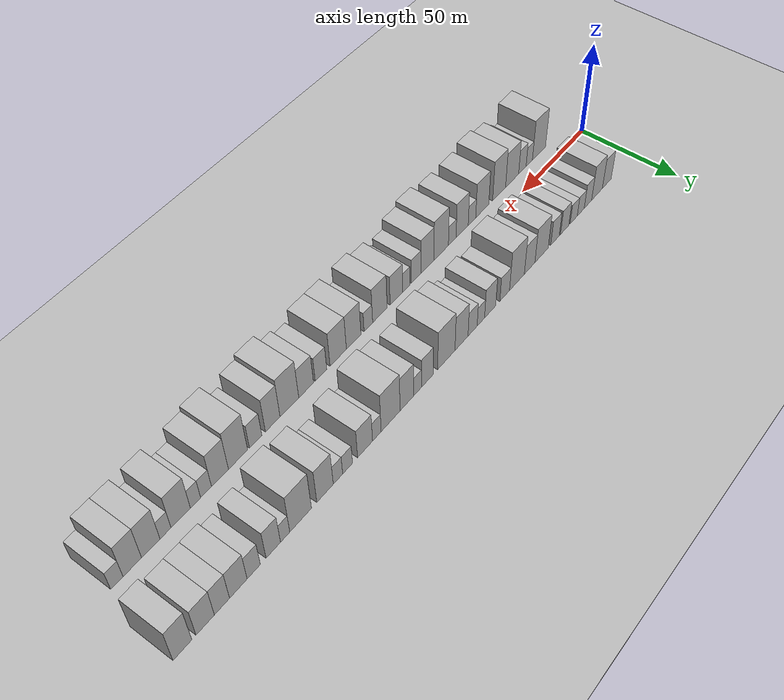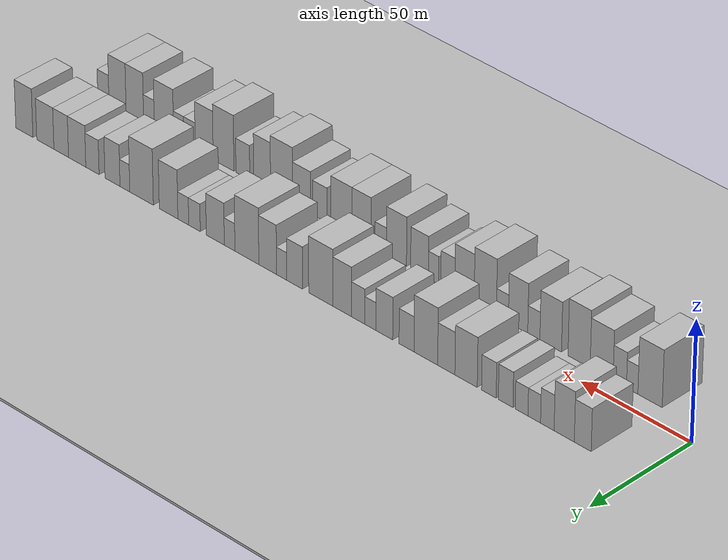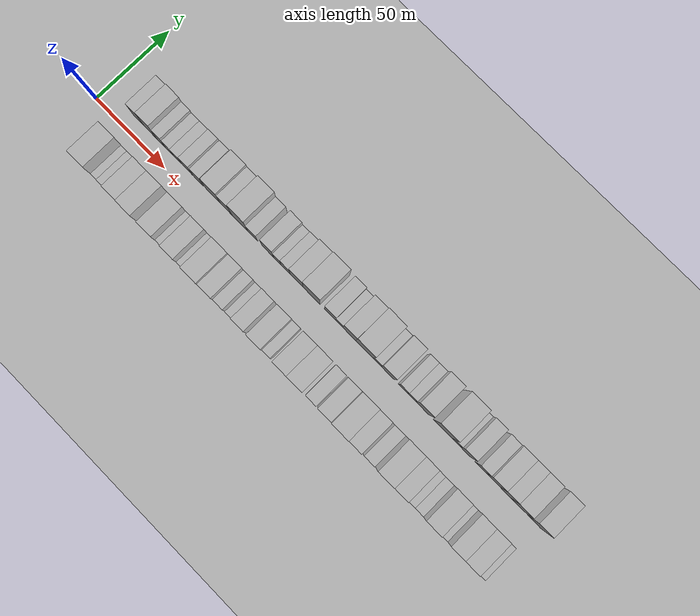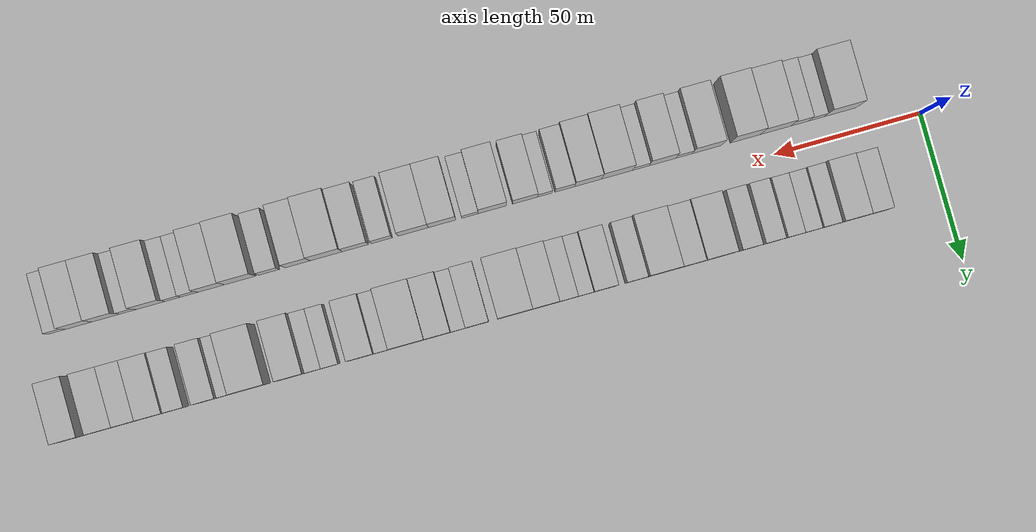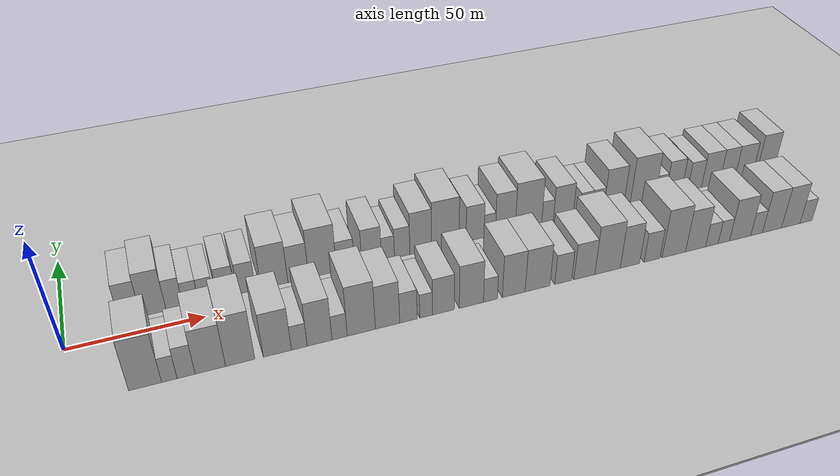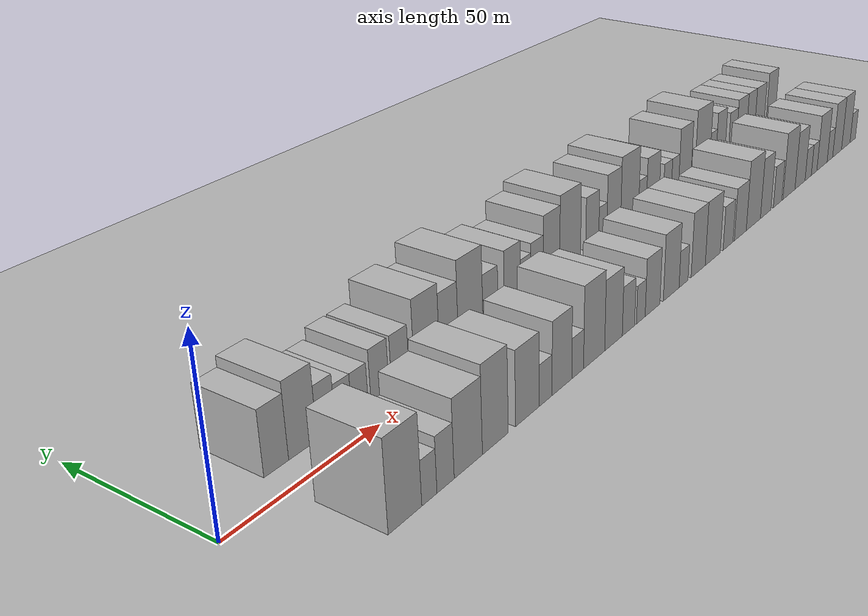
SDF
<?xml version="1.0" encoding="utf-8"?>

<sdf version="1.6">

   <world name="default">

      <gui fullscreen="0">

         <camera name="user_camera">

            <pose>-15 0 4.57585 0 0 0</pose>

            <view_controller>orbit</view_controller>

         </camera>

      </gui>

      <scene>

         <sky>

           <clouds>

             <speed>12</speed>

           </clouds>

         </sky>

         <ambient>0.4 0.4 0.4 1</ambient>

         <background>0.7 0.7 0.7 1</background>

         <shadows>1</shadows>

      </scene>

      <gravity>0 0 -9.8066</gravity>

      <magnetic_field>6e-06 2.3e-05 -4.2e-05</magnetic_field>

      <physics default="0" name="default_physics" type="ode">

         <ode>

            <solver>

               <type>quick</type>

               <iters>10</iters>

               <sor>1.0</sor>

               <use_dynamic_moi_rescaling>0</use_dynamic_moi_rescaling>

            </solver>

            <constraints>

               <cfm>0</cfm>

               <erp>0.2</erp>

               <contact_max_correcting_vel>100</contact_max_correcting_vel>

               <contact_surface_layer>0.001</contact_surface_layer>

            </constraints>

         </ode>

         <max_step_size>0.004</max_step_size>

         <real_time_factor>1</real_time_factor>

         <real_time_update_rate>250</real_time_update_rate>

      </physics>

      <light name="sun" type="directional">

         <cast_shadows>1</cast_shadows>

         <pose>0 0 10 0 0 0</pose>

         <diffuse>0.8 0.8 0.8 1</diffuse>

         <specular>0.2 0.2 0.2 1</specular>

         <attenuation>

            <range>1000</range>

            <constant>0.9</constant>

            <linear>0.01</linear>

            <quadratic>0.001</quadratic>

         </attenuation>

         <direction>-0.5 0.1 -0.9</direction>

      </light>

      <include>

         <name>ground_plane_1</name>

         <uri>model://HANNAS_ground_plane</uri>

         <pose>0 0 0  0 0 0</pose>

      </include>

      <include>

         <name>ground_plane_2</name>

         <uri>model://HANNAS_ground_plane</uri>

         <pose>100 0 0  0 0 0</pose>

      </include>

      <model name="building_1">

         <static>1</static>

         <pose frame="">23.8126 17.5000 0 0.000000 0.000000 1.570796</pose>

         <link name="link">

            <pose frame="">0 0 9.00 0 0 0</pose>

            <collision name="collision">

               <geometry>

                  <box>

                     <size>20.0000 7.6253 18.0000</size>

                  </box>

               </geometry>

               <max_contacts>10</max_contacts>

               <surface>

                  <contact>

                     <ode/>

                  </contact>

                  <bounce/>

                  <friction>

                     <torsional>

                        <ode/>

                     </torsional>

                     <ode/>

                  </friction>

               </surface>

            </collision>

            <visual name="visual">

               <cast_shadows>0</cast_shadows>

               <geometry>

                  <box>

                     <size>20.0000 7.6253 18.0000</size>

                  </box>

               </geometry>

               <material>

                  <script>

                     <uri>model://HANNAS_wall/materials/scripts</uri>

                     <uri>model://HANNAS_wall/materials/textures</uri>

                     <name>vrc/HANNAS_wall</name>

                  </script>

               </material>

            </visual>

            <self_collide>0</self_collide>

            <enable_wind>0</enable_wind>

            <kinematic>0</kinematic>

         </link>

      </model>

      <model name="building_2">

         <static>1</static>

         <pose frame="">32.1974 17.5000 0 0.000000 0.000000 1.570796</pose>

         <link name="link">

            <pose frame="">0 0 10.50 0 0 0</pose>

            <collision name="collision">

               <geometry>

                  <box>

                     <size>20.0000 9.1443 21.0000</size>

                  </box>

               </geometry>

               <max_contacts>10</max_contacts>

               <surface>

                  <contact>

                     <ode/>

                  </contact>

                  <bounce/>

                  <friction>

                     <torsional>

                        <ode/>

                     </torsional>

                     <ode/>

                  </friction>

               </surface>

            </collision>

            <visual name="visual">

               <cast_shadows>0</cast_shadows>

               <geometry>

                  <box>

                     <size>20.0000 9.1443 21.0000</size>

                  </box>

               </geometry>

               <material>

                  <script>

                     <uri>model://HANNAS_wall/materials/scripts</uri>

                     <uri>model://HANNAS_wall/materials/textures</uri>

                     <name>vrc/HANNAS_wall</name>

                  </script>

               </material>

            </visual>

            <self_collide>0</self_collide>

            <enable_wind>0</enable_wind>

            <kinematic>0</kinematic>

         </link>

      </model>

      <model name="building_3">

         <static>1</static>

         <pose frame="">39.8481 17.5000 0 0.000000 0.000000 1.570796</pose>

         <link name="link">

            <pose frame="">0 0 7.50 0 0 0</pose>

            <collision name="collision">

               <geometry>

                  <box>

                     <size>20.0000 6.1571 15.0000</size>

                  </box>

               </geometry>

               <max_contacts>10</max_contacts>

               <surface>

                  <contact>

                     <ode/>

                  </contact>

                  <bounce/>

                  <friction>

                     <torsional>

                        <ode/>

                     </torsional>

                     <ode/>

                  </friction>

               </surface>

            </collision>

            <visual name="visual">

               <cast_shadows>0</cast_shadows>

               <geometry>

                  <box>

                     <size>20.0000 6.1571 15.0000</size>

                  </box>

               </geometry>

               <material>

                  <script>

                     <uri>model://HANNAS_wall/materials/scripts</uri>

                     <uri>model://HANNAS_wall/materials/textures</uri>

                     <name>vrc/HANNAS_wall</name>

                  </script>

               </material>

            </visual>

            <self_collide>0</self_collide>

            <enable_wind>0</enable_wind>

            <kinematic>0</kinematic>

         </link>

      </model>

      <model name="building_4">

         <static>1</static>

         <pose frame="">45.8018 17.5000 0 0.000000 0.000000 1.570796</pose>

         <link name="link">

            <pose frame="">0 0 6.00 0 0 0</pose>

            <collision name="collision">

               <geometry>

                  <box>

                     <size>20.0000 5.7503 12.0000</size>

                  </box>

               </geometry>

               <max_contacts>10</max_contacts>

               <surface>

                  <contact>

                     <ode/>

                  </contact>

                  <bounce/>

                  <friction>

                     <torsional>

                        <ode/>

                     </torsional>

                     <ode/>

                  </friction>

               </surface>

            </collision>

            <visual name="visual">

               <cast_shadows>0</cast_shadows>

               <geometry>

                  <box>

                     <size>20.0000 5.7503 12.0000</size>

                  </box>

               </geometry>

               <material>

                  <script>

                     <uri>model://HANNAS_wall/materials/scripts</uri>

                     <uri>model://HANNAS_wall/materials/textures</uri>

                     <name>vrc/HANNAS_wall</name>

                  </script>

               </material>

            </visual>

            <self_collide>0</self_collide>

            <enable_wind>0</enable_wind>

            <kinematic>0</kinematic>

         </link>

      </model>

      <model name="building_5">

         <static>1</static>

         <pose frame="">51.6084 17.5000 0 0.000000 0.000000 1.570796</pose>

         <link name="link">

            <pose frame="">0 0 6.00 0 0 0</pose>

            <collision name="collision">

               <geometry>

                  <box>

                     <size>20.0000 5.8628 12.0000</size>

                  </box>

               </geometry>

               <max_contacts>10</max_contacts>

               <surface>

                  <contact>

                     <ode/>

                  </contact>

                  <bounce/>

                  <friction>

                     <torsional>

                        <ode/>

                     </torsional>

                     <ode/>

                  </friction>

               </surface>

            </collision>

            <visual name="visual">

               <cast_shadows>0</cast_shadows>

               <geometry>

                  <box>

                     <size>20.0000 5.8628 12.0000</size>

                  </box>

               </geometry>

               <material>

                  <script>

                     <uri>model://HANNAS_wall/materials/scripts</uri>

                     <uri>model://HANNAS_wall/materials/textures</uri>

                     <name>vrc/HANNAS_wall</name>

                  </script>

               </material>

            </visual>

            <self_collide>0</self_collide>

            <enable_wind>0</enable_wind>

            <kinematic>0</kinematic>

         </link>

      </model>

      <model name="building_6">

         <static>1</static>

         <pose frame="">58.9072 17.5000 0 0.000000 0.000000 1.570796</pose>

         <link name="link">

            <pose frame="">0 0 7.50 0 0 0</pose>

            <collision name="collision">

               <geometry>

                  <box>

                     <size>20.0000 6.7347 15.0000</size>

                  </box>

               </geometry>

               <max_contacts>10</max_contacts>

               <surface>

                  <contact>

                     <ode/>

                  </contact>

                  <bounce/>

                  <friction>

                     <torsional>

                        <ode/>

                     </torsional>

                     <ode/>

                  </friction>

               </surface>

            </collision>

            <visual name="visual">

               <cast_shadows>0</cast_shadows>

               <geometry>

                  <box>

                     <size>20.0000 6.7347 15.0000</size>

                  </box>

               </geometry>

               <material>

                  <script>

                     <uri>model://HANNAS_wall/materials/scripts</uri>

                     <uri>model://HANNAS_wall/materials/textures</uri>

                     <name>vrc/HANNAS_wall</name>

                  </script>

               </material>

            </visual>

            <self_collide>0</self_collide>

            <enable_wind>0</enable_wind>

            <kinematic>0</kinematic>

         </link>

      </model>

      <model name="building_7">

         <static>1</static>

         <pose frame="">66.6539 17.5000 0 0.000000 0.000000 1.570796</pose>

         <link name="link">

            <pose frame="">0 0 7.50 0 0 0</pose>

            <collision name="collision">

               <geometry>

                  <box>

                     <size>20.0000 6.7587 15.0000</size>

                  </box>

               </geometry>

               <max_contacts>10</max_contacts>

               <surface>

                  <contact>

                     <ode/>

                  </contact>

                  <bounce/>

                  <friction>

                     <torsional>

                        <ode/>

                     </torsional>

                     <ode/>

                  </friction>

               </surface>

            </collision>

            <visual name="visual">

               <cast_shadows>0</cast_shadows>

               <geometry>

                  <box>

                     <size>20.0000 6.7587 15.0000</size>

                  </box>

               </geometry>

               <material>

                  <script>

                     <uri>model://HANNAS_wall/materials/scripts</uri>

                     <uri>model://HANNAS_wall/materials/textures</uri>

                     <name>vrc/HANNAS_wall</name>

                  </script>

               </material>

            </visual>

            <self_collide>0</self_collide>

            <enable_wind>0</enable_wind>

            <kinematic>0</kinematic>

         </link>

      </model>

      <model name="building_8">

         <static>1</static>

         <pose frame="">77.2177 17.5000 0 0.000000 0.000000 1.570796</pose>

         <link name="link">

            <pose frame="">0 0 10.50 0 0 0</pose>

            <collision name="collision">

               <geometry>

                  <box>

                     <size>20.0000 10.3690 21.0000</size>

                  </box>

               </geometry>

               <max_contacts>10</max_contacts>

               <surface>

                  <contact>

                     <ode/>

                  </contact>

                  <bounce/>

                  <friction>

                     <torsional>

                        <ode/>

                     </torsional>

                     <ode/>

                  </friction>

               </surface>

            </collision>

            <visual name="visual">

               <cast_shadows>0</cast_shadows>

               <geometry>

                  <box>

                     <size>20.0000 10.3690 21.0000</size>

                  </box>

               </geometry>

               <material>

                  <script>

                     <uri>model://HANNAS_wall/materials/scripts</uri>

                     <uri>model://HANNAS_wall/materials/textures</uri>

                     <name>vrc/HANNAS_wall</name>

                  </script>

               </material>

            </visual>

            <self_collide>0</self_collide>

            <enable_wind>0</enable_wind>

            <kinematic>0</kinematic>

         </link>

      </model>

      <model name="building_9">

         <static>1</static>

         <pose frame="">86.4406 17.5000 0 0.000000 0.000000 1.570796</pose>

         <link name="link">

            <pose frame="">0 0 9.00 0 0 0</pose>

            <collision name="collision">

               <geometry>

                  <box>

                     <size>20.0000 8.0770 18.0000</size>

                  </box>

               </geometry>

               <max_contacts>10</max_contacts>

               <surface>

                  <contact>

                     <ode/>

                  </contact>

                  <bounce/>

                  <friction>

                     <torsional>

                        <ode/>

                     </torsional>

                     <ode/>

                  </friction>

               </surface>

            </collision>

            <visual name="visual">

               <cast_shadows>0</cast_shadows>

               <geometry>

                  <box>

                     <size>20.0000 8.0770 18.0000</size>

                  </box>

               </geometry>

               <material>

                  <script>

                     <uri>model://HANNAS_wall/materials/scripts</uri>

                     <uri>model://HANNAS_wall/materials/textures</uri>

                     <name>vrc/HANNAS_wall</name>

                  </script>

               </material>

            </visual>

            <self_collide>0</self_collide>

            <enable_wind>0</enable_wind>

            <kinematic>0</kinematic>

         </link>

      </model>

      <model name="building_10">

         <static>1</static>

         <pose frame="">96.0227 17.5000 0 0.000000 0.000000 1.570796</pose>

         <link name="link">

            <pose frame="">0 0 12.00 0 0 0</pose>

            <collision name="collision">

               <geometry>

                  <box>

                     <size>20.0000 11.0871 24.0000</size>

                  </box>

               </geometry>

               <max_contacts>10</max_contacts>

               <surface>

                  <contact>

                     <ode/>

                  </contact>

                  <bounce/>

                  <friction>

                     <torsional>

                        <ode/>

                     </torsional>

                     <ode/>

                  </friction>

               </surface>

            </collision>

            <visual name="visual">

               <cast_shadows>0</cast_shadows>

               <geometry>

                  <box>

                     <size>20.0000 11.0871 24.0000</size>

                  </box>

               </geometry>

               <material>

                  <script>

                     <uri>model://HANNAS_wall/materials/scripts</uri>

                     <uri>model://HANNAS_wall/materials/textures</uri>

                     <name>vrc/HANNAS_wall</name>

                  </script>

               </material>

            </visual>

            <self_collide>0</self_collide>

            <enable_wind>0</enable_wind>

            <kinematic>0</kinematic>

         </link>

      </model>

      <model name="building_11">

         <static>1</static>

         <pose frame="">105.1136 17.5000 0 0.000000 0.000000 1.570796</pose>

         <link name="link">

            <pose frame="">0 0 7.50 0 0 0</pose>

            <collision name="collision">

               <geometry>

                  <box>

                     <size>20.0000 7.0948 15.0000</size>

                  </box>

               </geometry>

               <max_contacts>10</max_contacts>

               <surface>

                  <contact>

                     <ode/>

                  </contact>

                  <bounce/>

                  <friction>

                     <torsional>

                        <ode/>

                     </torsional>

                     <ode/>

                  </friction>

               </surface>

            </collision>

            <visual name="visual">

               <cast_shadows>0</cast_shadows>

               <geometry>

                  <box>

                     <size>20.0000 7.0948 15.0000</size>

                  </box>

               </geometry>

               <material>

                  <script>

                     <uri>model://HANNAS_wall/materials/scripts</uri>

                     <uri>model://HANNAS_wall/materials/textures</uri>

                     <name>vrc/HANNAS_wall</name>

                  </script>

               </material>

            </visual>

            <self_collide>0</self_collide>

            <enable_wind>0</enable_wind>

            <kinematic>0</kinematic>

         </link>

      </model>

      <model name="building_12">

         <static>1</static>

         <pose frame="">115.6611 17.5000 0 0.000000 0.000000 1.570796</pose>

         <link name="link">

            <pose frame="">0 0 9.00 0 0 0</pose>

            <collision name="collision">

               <geometry>

                  <box>

                     <size>20.0000 8.0001 18.0000</size>

                  </box>

               </geometry>

               <max_contacts>10</max_contacts>

               <surface>

                  <contact>

                     <ode/>

                  </contact>

                  <bounce/>

                  <friction>

                     <torsional>

                        <ode/>

                     </torsional>

                     <ode/>

                  </friction>

               </surface>

            </collision>

            <visual name="visual">

               <cast_shadows>0</cast_shadows>

               <geometry>

                  <box>

                     <size>20.0000 8.0001 18.0000</size>

                  </box>

               </geometry>

               <material>

                  <script>

                     <uri>model://HANNAS_wall/materials/scripts</uri>

                     <uri>model://HANNAS_wall/materials/textures</uri>

                     <name>vrc/HANNAS_wall</name>

                  </script>

               </material>

            </visual>

            <self_collide>0</self_collide>

            <enable_wind>0</enable_wind>

            <kinematic>0</kinematic>

         </link>

      </model>

      <model name="building_13">

         <static>1</static>

         <pose frame="">122.2943 17.5000 0 0.000000 0.000000 1.570796</pose>

         <link name="link">

            <pose frame="">0 0 6.00 0 0 0</pose>

            <collision name="collision">

               <geometry>

                  <box>

                     <size>20.0000 5.2664 12.0000</size>

                  </box>

               </geometry>

               <max_contacts>10</max_contacts>

               <surface>

                  <contact>

                     <ode/>

                  </contact>

                  <bounce/>

                  <friction>

                     <torsional>

                        <ode/>

                     </torsional>

                     <ode/>

                  </friction>

               </surface>

            </collision>

            <visual name="visual">

               <cast_shadows>0</cast_shadows>

               <geometry>

                  <box>

                     <size>20.0000 5.2664 12.0000</size>

                  </box>

               </geometry>

               <material>

                  <script>

                     <uri>model://HANNAS_wall/materials/scripts</uri>

                     <uri>model://HANNAS_wall/materials/textures</uri>

                     <name>vrc/HANNAS_wall</name>

                  </script>

               </material>

            </visual>

            <self_collide>0</self_collide>

            <enable_wind>0</enable_wind>

            <kinematic>0</kinematic>

         </link>

      </model>

      <model name="building_14">

         <static>1</static>

         <pose frame="">128.1226 17.5000 0 0.000000 0.000000 1.570796</pose>

         <link name="link">

            <pose frame="">0 0 7.50 0 0 0</pose>

            <collision name="collision">

               <geometry>

                  <box>

                     <size>20.0000 6.3901 15.0000</size>

                  </box>

               </geometry>

               <max_contacts>10</max_contacts>

               <surface>

                  <contact>

                     <ode/>

                  </contact>

                  <bounce/>

                  <friction>

                     <torsional>

                        <ode/>

                     </torsional>

                     <ode/>

                  </friction>

               </surface>

            </collision>

            <visual name="visual">

               <cast_shadows>0</cast_shadows>

               <geometry>

                  <box>

                     <size>20.0000 6.3901 15.0000</size>

                  </box>

               </geometry>

               <material>

                  <script>

                     <uri>model://HANNAS_wall/materials/scripts</uri>

                     <uri>model://HANNAS_wall/materials/textures</uri>

                     <name>vrc/HANNAS_wall</name>

                  </script>

               </material>

            </visual>

            <self_collide>0</self_collide>

            <enable_wind>0</enable_wind>

            <kinematic>0</kinematic>

         </link>

      </model>

      <model name="building_15">

         <static>1</static>

         <pose frame="">135.8047 17.5000 0 0.000000 0.000000 1.570796</pose>

         <link name="link">

            <pose frame="">0 0 10.50 0 0 0</pose>

            <collision name="collision">

               <geometry>

                  <box>

                     <size>20.0000 8.9742 21.0000</size>

                  </box>

               </geometry>

               <max_contacts>10</max_contacts>

               <surface>

                  <contact>

                     <ode/>

                  </contact>

                  <bounce/>

                  <friction>

                     <torsional>

                        <ode/>

                     </torsional>

                     <ode/>

                  </friction>

               </surface>

            </collision>

            <visual name="visual">

               <cast_shadows>0</cast_shadows>

               <geometry>

                  <box>

                     <size>20.0000 8.9742 21.0000</size>

                  </box>

               </geometry>

               <material>

                  <script>

                     <uri>model://HANNAS_wall/materials/scripts</uri>

                     <uri>model://HANNAS_wall/materials/textures</uri>

                     <name>vrc/HANNAS_wall</name>

                  </script>

               </material>

            </visual>

            <self_collide>0</self_collide>

            <enable_wind>0</enable_wind>

            <kinematic>0</kinematic>

         </link>

      </model>

      <model name="building_16">

         <static>1</static>

         <pose frame="">146.1201 17.5000 0 0.000000 0.000000 1.570796</pose>

         <link name="link">

            <pose frame="">0 0 12.00 0 0 0</pose>

            <collision name="collision">

               <geometry>

                  <box>

                     <size>20.0000 11.6566 24.0000</size>

                  </box>

               </geometry>

               <max_contacts>10</max_contacts>

               <surface>

                  <contact>

                     <ode/>

                  </contact>

                  <bounce/>

                  <friction>

                     <torsional>

                        <ode/>

                     </torsional>

                     <ode/>

                  </friction>

               </surface>

            </collision>

            <visual name="visual">

               <cast_shadows>0</cast_shadows>

               <geometry>

                  <box>

                     <size>20.0000 11.6566 24.0000</size>

                  </box>

               </geometry>

               <material>

                  <script>

                     <uri>model://HANNAS_wall/materials/scripts</uri>

                     <uri>model://HANNAS_wall/materials/textures</uri>

                     <name>vrc/HANNAS_wall</name>

                  </script>

               </material>

            </visual>

            <self_collide>0</self_collide>

            <enable_wind>0</enable_wind>

            <kinematic>0</kinematic>

         </link>

      </model>

      <model name="building_17">

         <static>1</static>

         <pose frame="">158.8195 17.5000 0 0.000000 0.000000 1.570796</pose>

         <link name="link">

            <pose frame="">0 0 9.00 0 0 0</pose>

            <collision name="collision">

               <geometry>

                  <box>

                     <size>20.0000 7.7421 18.0000</size>

                  </box>

               </geometry>

               <max_contacts>10</max_contacts>

               <surface>

                  <contact>

                     <ode/>

                  </contact>

                  <bounce/>

                  <friction>

                     <torsional>

                        <ode/>

                     </torsional>

                     <ode/>

                  </friction>

               </surface>

            </collision>

            <visual name="visual">

               <cast_shadows>0</cast_shadows>

               <geometry>

                  <box>

                     <size>20.0000 7.7421 18.0000</size>

                  </box>

               </geometry>

               <material>

                  <script>

                     <uri>model://HANNAS_wall/materials/scripts</uri>

                     <uri>model://HANNAS_wall/materials/textures</uri>

                     <name>vrc/HANNAS_wall</name>

                  </script>

               </material>

            </visual>

            <self_collide>0</self_collide>

            <enable_wind>0</enable_wind>

            <kinematic>0</kinematic>

         </link>

      </model>

      <model name="building_18">

         <static>1</static>

         <pose frame="">165.1507 17.5000 0 0.000000 0.000000 1.570796</pose>

         <link name="link">

            <pose frame="">0 0 6.00 0 0 0</pose>

            <collision name="collision">

               <geometry>

                  <box>

                     <size>20.0000 4.9204 12.0000</size>

                  </box>

               </geometry>

               <max_contacts>10</max_contacts>

               <surface>

                  <contact>

                     <ode/>

                  </contact>

                  <bounce/>

                  <friction>

                     <torsional>

                        <ode/>

                     </torsional>

                     <ode/>

                  </friction>

               </surface>

            </collision>

            <visual name="visual">

               <cast_shadows>0</cast_shadows>

               <geometry>

                  <box>

                     <size>20.0000 4.9204 12.0000</size>

                  </box>

               </geometry>

               <material>

                  <script>

                     <uri>model://HANNAS_wall/materials/scripts</uri>

                     <uri>model://HANNAS_wall/materials/textures</uri>

                     <name>vrc/HANNAS_wall</name>

                  </script>

               </material>

            </visual>

            <self_collide>0</self_collide>

            <enable_wind>0</enable_wind>

            <kinematic>0</kinematic>

         </link>

      </model>

      <model name="building_19">

         <static>1</static>

         <pose frame="">171.9484 17.5000 0 0.000000 0.000000 1.570796</pose>

         <link name="link">

            <pose frame="">0 0 10.50 0 0 0</pose>

            <collision name="collision">

               <geometry>

                  <box>

                     <size>20.0000 8.6751 21.0000</size>

                  </box>

               </geometry>

               <max_contacts>10</max_contacts>

               <surface>

                  <contact>

                     <ode/>

                  </contact>

                  <bounce/>

                  <friction>

                     <torsional>

                        <ode/>

                     </torsional>

                     <ode/>

                  </friction>

               </surface>

            </collision>

            <visual name="visual">

               <cast_shadows>0</cast_shadows>

               <geometry>

                  <box>

                     <size>20.0000 8.6751 21.0000</size>

                  </box>

               </geometry>

               <material>

                  <script>

                     <uri>model://HANNAS_wall/materials/scripts</uri>

                     <uri>model://HANNAS_wall/materials/textures</uri>

                     <name>vrc/HANNAS_wall</name>

                  </script>

               </material>

            </visual>

            <self_collide>0</self_collide>

            <enable_wind>0</enable_wind>

            <kinematic>0</kinematic>

         </link>

      </model>

      <model name="building_20">

         <static>1</static>

         <pose frame="">182.1808 17.5000 0 0.000000 0.000000 1.570796</pose>

         <link name="link">

            <pose frame="">0 0 12.00 0 0 0</pose>

            <collision name="collision">

               <geometry>

                  <box>

                     <size>20.0000 11.7897 24.0000</size>

                  </box>

               </geometry>

               <max_contacts>10</max_contacts>

               <surface>

                  <contact>

                     <ode/>

                  </contact>

                  <bounce/>

                  <friction>

                     <torsional>

                        <ode/>

                     </torsional>

                     <ode/>

                  </friction>

               </surface>

            </collision>

            <visual name="visual">

               <cast_shadows>0</cast_shadows>

               <geometry>

                  <box>

                     <size>20.0000 11.7897 24.0000</size>

                  </box>

               </geometry>

               <material>

                  <script>

                     <uri>model://HANNAS_wall/materials/scripts</uri>

                     <uri>model://HANNAS_wall/materials/textures</uri>

                     <name>vrc/HANNAS_wall</name>

                  </script>

               </material>

            </visual>

            <self_collide>0</self_collide>

            <enable_wind>0</enable_wind>

            <kinematic>0</kinematic>

         </link>

      </model>

      <model name="building_21">

         <static>1</static>

         <pose frame="">190.7075 17.5000 0 0.000000 0.000000 1.570796</pose>

         <link name="link">

            <pose frame="">0 0 6.00 0 0 0</pose>

            <collision name="collision">

               <geometry>

                  <box>

                     <size>20.0000 5.2637 12.0000</size>

                  </box>

               </geometry>

               <max_contacts>10</max_contacts>

               <surface>

                  <contact>

                     <ode/>

                  </contact>

                  <bounce/>

                  <friction>

                     <torsional>

                        <ode/>

                     </torsional>

                     <ode/>

                  </friction>

               </surface>

            </collision>

            <visual name="visual">

               <cast_shadows>0</cast_shadows>

               <geometry>

                  <box>

                     <size>20.0000 5.2637 12.0000</size>

                  </box>

               </geometry>

               <material>

                  <script>

                     <uri>model://HANNAS_wall/materials/scripts</uri>

                     <uri>model://HANNAS_wall/materials/textures</uri>

                     <name>vrc/HANNAS_wall</name>

                  </script>

               </material>

            </visual>

            <self_collide>0</self_collide>

            <enable_wind>0</enable_wind>

            <kinematic>0</kinematic>

         </link>

      </model>

      <model name="building_22">

         <static>1</static>

         <pose frame="">197.8259 17.5000 0 0.000000 0.000000 1.570796</pose>

         <link name="link">

            <pose frame="">0 0 9.00 0 0 0</pose>

            <collision name="collision">

               <geometry>

                  <box>

                     <size>20.0000 8.9731 18.0000</size>

                  </box>

               </geometry>

               <max_contacts>10</max_contacts>

               <surface>

                  <contact>

                     <ode/>

                  </contact>

                  <bounce/>

                  <friction>

                     <torsional>

                        <ode/>

                     </torsional>

                     <ode/>

                  </friction>

               </surface>

            </collision>

            <visual name="visual">

               <cast_shadows>0</cast_shadows>

               <geometry>

                  <box>

                     <size>20.0000 8.9731 18.0000</size>

                  </box>

               </geometry>

               <material>

                  <script>

                     <uri>model://HANNAS_wall/materials/scripts</uri>

                     <uri>model://HANNAS_wall/materials/textures</uri>

                     <name>vrc/HANNAS_wall</name>

                  </script>

               </material>

            </visual>

            <self_collide>0</self_collide>

            <enable_wind>0</enable_wind>

            <kinematic>0</kinematic>

         </link>

      </model>

      <model name="building_23">

         <static>1</static>

         <pose frame="">208.1990 17.5000 0 0.000000 0.000000 1.570796</pose>

         <link name="link">

            <pose frame="">0 0 6.00 0 0 0</pose>

            <collision name="collision">

               <geometry>

                  <box>

                     <size>20.0000 5.7732 12.0000</size>

                  </box>

               </geometry>

               <max_contacts>10</max_contacts>

               <surface>

                  <contact>

                     <ode/>

                  </contact>

                  <bounce/>

                  <friction>

                     <torsional>

                        <ode/>

                     </torsional>

                     <ode/>

                  </friction>

               </surface>

            </collision>

            <visual name="visual">

               <cast_shadows>0</cast_shadows>

               <geometry>

                  <box>

                     <size>20.0000 5.7732 12.0000</size>

                  </box>

               </geometry>

               <material>

                  <script>

                     <uri>model://HANNAS_wall/materials/scripts</uri>

                     <uri>model://HANNAS_wall/materials/textures</uri>

                     <name>vrc/HANNAS_wall</name>

                  </script>

               </material>

            </visual>

            <self_collide>0</self_collide>

            <enable_wind>0</enable_wind>

            <kinematic>0</kinematic>

         </link>

      </model>

      <model name="building_24">

         <static>1</static>

         <pose frame="">213.7987 17.5000 0 0.000000 0.000000 1.570796</pose>

         <link name="link">

            <pose frame="">0 0 6.00 0 0 0</pose>

            <collision name="collision">

               <geometry>

                  <box>

                     <size>20.0000 5.4261 12.0000</size>

                  </box>

               </geometry>

               <max_contacts>10</max_contacts>

               <surface>

                  <contact>

                     <ode/>

                  </contact>

                  <bounce/>

                  <friction>

                     <torsional>

                        <ode/>

                     </torsional>

                     <ode/>

                  </friction>

               </surface>

            </collision>

            <visual name="visual">

               <cast_shadows>0</cast_shadows>

               <geometry>

                  <box>

                     <size>20.0000 5.4261 12.0000</size>

                  </box>

               </geometry>

               <material>

                  <script>

                     <uri>model://HANNAS_wall/materials/scripts</uri>

                     <uri>model://HANNAS_wall/materials/textures</uri>

                     <name>vrc/HANNAS_wall</name>

                  </script>

               </material>

            </visual>

            <self_collide>0</self_collide>

            <enable_wind>0</enable_wind>

            <kinematic>0</kinematic>

         </link>

      </model>

      <model name="building_25">

         <static>1</static>

         <pose frame="">221.1981 17.5000 0 0.000000 0.000000 1.570796</pose>

         <link name="link">

            <pose frame="">0 0 10.50 0 0 0</pose>

            <collision name="collision">

               <geometry>

                  <box>

                     <size>20.0000 9.3727 21.0000</size>

                  </box>

               </geometry>

               <max_contacts>10</max_contacts>

               <surface>

                  <contact>

                     <ode/>

                  </contact>

                  <bounce/>

                  <friction>

                     <torsional>

                        <ode/>

                     </torsional>

                     <ode/>

                  </friction>

               </surface>

            </collision>

            <visual name="visual">

               <cast_shadows>0</cast_shadows>

               <geometry>

                  <box>

                     <size>20.0000 9.3727 21.0000</size>

                  </box>

               </geometry>

               <material>

                  <script>

                     <uri>model://HANNAS_wall/materials/scripts</uri>

                     <uri>model://HANNAS_wall/materials/textures</uri>

                     <name>vrc/HANNAS_wall</name>

                  </script>

               </material>

            </visual>

            <self_collide>0</self_collide>

            <enable_wind>0</enable_wind>

            <kinematic>0</kinematic>

         </link>

      </model>

      <model name="building_26">

         <static>1</static>

         <pose frame="">234.8552 17.5000 0 0.000000 0.000000 1.570796</pose>

         <link name="link">

            <pose frame="">0 0 12.00 0 0 0</pose>

            <collision name="collision">

               <geometry>

                  <box>

                     <size>20.0000 11.9416 24.0000</size>

                  </box>

               </geometry>

               <max_contacts>10</max_contacts>

               <surface>

                  <contact>

                     <ode/>

                  </contact>

                  <bounce/>

                  <friction>

                     <torsional>

                        <ode/>

                     </torsional>

                     <ode/>

                  </friction>

               </surface>

            </collision>

            <visual name="visual">

               <cast_shadows>0</cast_shadows>

               <geometry>

                  <box>

                     <size>20.0000 11.9416 24.0000</size>

                  </box>

               </geometry>

               <material>

                  <script>

                     <uri>model://HANNAS_wall/materials/scripts</uri>

                     <uri>model://HANNAS_wall/materials/textures</uri>

                     <name>vrc/HANNAS_wall</name>

                  </script>

               </material>

            </visual>

            <self_collide>0</self_collide>

            <enable_wind>0</enable_wind>

            <kinematic>0</kinematic>

         </link>

      </model>

      <model name="building_27">

         <static>1</static>

         <pose frame="">243.3277 17.5000 0 0.000000 0.000000 1.570796</pose>

         <link name="link">

            <pose frame="">0 0 6.00 0 0 0</pose>

            <collision name="collision">

               <geometry>

                  <box>

                     <size>20.0000 5.0033 12.0000</size>

                  </box>

               </geometry>

               <max_contacts>10</max_contacts>

               <surface>

                  <contact>

                     <ode/>

                  </contact>

                  <bounce/>

                  <friction>

                     <torsional>

                        <ode/>

                     </torsional>

                     <ode/>

                  </friction>

               </surface>

            </collision>

            <visual name="visual">

               <cast_shadows>0</cast_shadows>

               <geometry>

                  <box>

                     <size>20.0000 5.0033 12.0000</size>

                  </box>

               </geometry>

               <material>

                  <script>

                     <uri>model://HANNAS_wall/materials/scripts</uri>

                     <uri>model://HANNAS_wall/materials/textures</uri>

                     <name>vrc/HANNAS_wall</name>

                  </script>

               </material>

            </visual>

            <self_collide>0</self_collide>

            <enable_wind>0</enable_wind>

            <kinematic>0</kinematic>

         </link>

      </model>

      <model name="building_28">

         <static>1</static>

         <pose frame="">249.6791 17.5000 0 0.000000 0.000000 1.570796</pose>

         <link name="link">

            <pose frame="">0 0 9.00 0 0 0</pose>

            <collision name="collision">

               <geometry>

                  <box>

                     <size>20.0000 7.6994 18.0000</size>

                  </box>

               </geometry>

               <max_contacts>10</max_contacts>

               <surface>

                  <contact>

                     <ode/>

                  </contact>

                  <bounce/>

                  <friction>

                     <torsional>

                        <ode/>

                     </torsional>

                     <ode/>

                  </friction>

               </surface>

            </collision>

            <visual name="visual">

               <cast_shadows>0</cast_shadows>

               <geometry>

                  <box>

                     <size>20.0000 7.6994 18.0000</size>

                  </box>

               </geometry>

               <material>

                  <script>

                     <uri>model://HANNAS_wall/materials/scripts</uri>

                     <uri>model://HANNAS_wall/materials/textures</uri>

                     <name>vrc/HANNAS_wall</name>

                  </script>

               </material>

            </visual>

            <self_collide>0</self_collide>

            <enable_wind>0</enable_wind>

            <kinematic>0</kinematic>

         </link>

      </model>

      <model name="building_29">

         <static>1</static>

         <pose frame="">259.9456 17.5000 0 0.000000 0.000000 1.570796</pose>

         <link name="link">

            <pose frame="">0 0 7.50 0 0 0</pose>

            <collision name="collision">

               <geometry>

                  <box>

                     <size>20.0000 6.8336 15.0000</size>

                  </box>

               </geometry>

               <max_contacts>10</max_contacts>

               <surface>

                  <contact>

                     <ode/>

                  </contact>

                  <bounce/>

                  <friction>

                     <torsional>

                        <ode/>

                     </torsional>

                     <ode/>

                  </friction>

               </surface>

            </collision>

            <visual name="visual">

               <cast_shadows>0</cast_shadows>

               <geometry>

                  <box>

                     <size>20.0000 6.8336 15.0000</size>

                  </box>

               </geometry>

               <material>

                  <script>

                     <uri>model://HANNAS_wall/materials/scripts</uri>

                     <uri>model://HANNAS_wall/materials/textures</uri>

                     <name>vrc/HANNAS_wall</name>

                  </script>

               </material>

            </visual>

            <self_collide>0</self_collide>

            <enable_wind>0</enable_wind>

            <kinematic>0</kinematic>

         </link>

      </model>

      <model name="building_30">

         <static>1</static>

         <pose frame="">267.8288 17.5000 0 0.000000 0.000000 1.570796</pose>

         <link name="link">

            <pose frame="">0 0 9.00 0 0 0</pose>

            <collision name="collision">

               <geometry>

                  <box>

                     <size>20.0000 8.9329 18.0000</size>

                  </box>

               </geometry>

               <max_contacts>10</max_contacts>

               <surface>

                  <contact>

                     <ode/>

                  </contact>

                  <bounce/>

                  <friction>

                     <torsional>

                        <ode/>

                     </torsional>

                     <ode/>

                  </friction>

               </surface>

            </collision>

            <visual name="visual">

               <cast_shadows>0</cast_shadows>

               <geometry>

                  <box>

                     <size>20.0000 8.9329 18.0000</size>

                  </box>

               </geometry>

               <material>

                  <script>

                     <uri>model://HANNAS_wall/materials/scripts</uri>

                     <uri>model://HANNAS_wall/materials/textures</uri>

                     <name>vrc/HANNAS_wall</name>

                  </script>

               </material>

            </visual>

            <self_collide>0</self_collide>

            <enable_wind>0</enable_wind>

            <kinematic>0</kinematic>

         </link>

      </model>

      <model name="building_31">

         <static>1</static>

         <pose frame="">276.0815 17.5000 0 0.000000 0.000000 1.570796</pose>

         <link name="link">

            <pose frame="">0 0 9.00 0 0 0</pose>

            <collision name="collision">

               <geometry>

                  <box>

                     <size>20.0000 7.5723 18.0000</size>

                  </box>

               </geometry>

               <max_contacts>10</max_contacts>

               <surface>

                  <contact>

                     <ode/>

                  </contact>

                  <bounce/>

                  <friction>

                     <torsional>

                        <ode/>

                     </torsional>

                     <ode/>

                  </friction>

               </surface>

            </collision>

            <visual name="visual">

               <cast_shadows>0</cast_shadows>

               <geometry>

                  <box>

                     <size>20.0000 7.5723 18.0000</size>

                  </box>

               </geometry>

               <material>

                  <script>

                     <uri>model://HANNAS_wall/materials/scripts</uri>

                     <uri>model://HANNAS_wall/materials/textures</uri>

                     <name>vrc/HANNAS_wall</name>

                  </script>

               </material>

            </visual>

            <self_collide>0</self_collide>

            <enable_wind>0</enable_wind>

            <kinematic>0</kinematic>

         </link>

      </model>

      <model name="building_32">

         <static>1</static>

         <pose frame="">284.3451 17.5000 0 0.000000 0.000000 1.570796</pose>

         <link name="link">

            <pose frame="">0 0 9.00 0 0 0</pose>

            <collision name="collision">

               <geometry>

                  <box>

                     <size>20.0000 8.9550 18.0000</size>

                  </box>

               </geometry>

               <max_contacts>10</max_contacts>

               <surface>

                  <contact>

                     <ode/>

                  </contact>

                  <bounce/>

                  <friction>

                     <torsional>

                        <ode/>

                     </torsional>

                     <ode/>

                  </friction>

               </surface>

            </collision>

            <visual name="visual">

               <cast_shadows>0</cast_shadows>

               <geometry>

                  <box>

                     <size>20.0000 8.9550 18.0000</size>

                  </box>

               </geometry>

               <material>

                  <script>

                     <uri>model://HANNAS_wall/materials/scripts</uri>

                     <uri>model://HANNAS_wall/materials/textures</uri>

                     <name>vrc/HANNAS_wall</name>

                  </script>

               </material>

            </visual>

            <self_collide>0</self_collide>

            <enable_wind>0</enable_wind>

            <kinematic>0</kinematic>

         </link>

      </model>

      <model name="building_33">

         <static>1</static>

         <pose frame="">295.3060 17.5000 0 0.000000 0.000000 1.570796</pose>

         <link name="link">

            <pose frame="">0 0 10.50 0 0 0</pose>

            <collision name="collision">

               <geometry>

                  <box>

                     <size>20.0000 8.9669 21.0000</size>

                  </box>

               </geometry>

               <max_contacts>10</max_contacts>

               <surface>

                  <contact>

                     <ode/>

                  </contact>

                  <bounce/>

                  <friction>

                     <torsional>

                        <ode/>

                     </torsional>

                     <ode/>

                  </friction>

               </surface>

            </collision>

            <visual name="visual">

               <cast_shadows>0</cast_shadows>

               <geometry>

                  <box>

                     <size>20.0000 8.9669 21.0000</size>

                  </box>

               </geometry>

               <material>

                  <script>

                     <uri>model://HANNAS_wall/materials/scripts</uri>

                     <uri>model://HANNAS_wall/materials/textures</uri>

                     <name>vrc/HANNAS_wall</name>

                  </script>

               </material>

            </visual>

            <self_collide>0</self_collide>

            <enable_wind>0</enable_wind>

            <kinematic>0</kinematic>

         </link>

      </model>

      <model name="building_34">

         <static>1</static>

         <pose frame="">25.4895 -17.5000 0 0.000000 0.000000 1.570796</pose>

         <link name="link">

            <pose frame="">0 0 12.00 0 0 0</pose>

            <collision name="collision">

               <geometry>

                  <box>

                     <size>20.0000 10.9790 24.0000</size>

                  </box>

               </geometry>

               <max_contacts>10</max_contacts>

               <surface>

                  <contact>

                     <ode/>

                  </contact>

                  <bounce/>

                  <friction>

                     <torsional>

                        <ode/>

                     </torsional>

                     <ode/>

                  </friction>

               </surface>

            </collision>

            <visual name="visual">

               <cast_shadows>0</cast_shadows>

               <geometry>

                  <box>

                     <size>20.0000 10.9790 24.0000</size>

                  </box>

               </geometry>

               <material>

                  <script>

                     <uri>model://HANNAS_wall/materials/scripts</uri>

                     <uri>model://HANNAS_wall/materials/textures</uri>

                     <name>vrc/HANNAS_wall</name>

                  </script>

               </material>

            </visual>

            <self_collide>0</self_collide>

            <enable_wind>0</enable_wind>

            <kinematic>0</kinematic>

         </link>

      </model>

      <model name="building_35">

         <static>1</static>

         <pose frame="">33.5721 -17.5000 0 0.000000 0.000000 1.570796</pose>

         <link name="link">

            <pose frame="">0 0 6.00 0 0 0</pose>

            <collision name="collision">

               <geometry>

                  <box>

                     <size>20.0000 5.1862 12.0000</size>

                  </box>

               </geometry>

               <max_contacts>10</max_contacts>

               <surface>

                  <contact>

                     <ode/>

                  </contact>

                  <bounce/>

                  <friction>

                     <torsional>

                        <ode/>

                     </torsional>

                     <ode/>

                  </friction>

               </surface>

            </collision>

            <visual name="visual">

               <cast_shadows>0</cast_shadows>

               <geometry>

                  <box>

                     <size>20.0000 5.1862 12.0000</size>

                  </box>

               </geometry>

               <material>

                  <script>

                     <uri>model://HANNAS_wall/materials/scripts</uri>

                     <uri>model://HANNAS_wall/materials/textures</uri>

                     <name>vrc/HANNAS_wall</name>

                  </script>

               </material>

            </visual>

            <self_collide>0</self_collide>

            <enable_wind>0</enable_wind>

            <kinematic>0</kinematic>

         </link>

      </model>

      <model name="building_36">

         <static>1</static>

         <pose frame="">39.2167 -17.5000 0 0.000000 0.000000 1.570796</pose>

         <link name="link">

            <pose frame="">0 0 7.50 0 0 0</pose>

            <collision name="collision">

               <geometry>

                  <box>

                     <size>20.0000 6.1029 15.0000</size>

                  </box>

               </geometry>

               <max_contacts>10</max_contacts>

               <surface>

                  <contact>

                     <ode/>

                  </contact>

                  <bounce/>

                  <friction>

                     <torsional>

                        <ode/>

                     </torsional>

                     <ode/>

                  </friction>

               </surface>

            </collision>

            <visual name="visual">

               <cast_shadows>0</cast_shadows>

               <geometry>

                  <box>

                     <size>20.0000 6.1029 15.0000</size>

                  </box>

               </geometry>

               <material>

                  <script>

                     <uri>model://HANNAS_wall/materials/scripts</uri>

                     <uri>model://HANNAS_wall/materials/textures</uri>

                     <name>vrc/HANNAS_wall</name>

                  </script>

               </material>

            </visual>

            <self_collide>0</self_collide>

            <enable_wind>0</enable_wind>

            <kinematic>0</kinematic>

         </link>

      </model>

      <model name="building_37">

         <static>1</static>

         <pose frame="">47.5106 -17.5000 0 0.000000 0.000000 1.570796</pose>

         <link name="link">

            <pose frame="">0 0 10.50 0 0 0</pose>

            <collision name="collision">

               <geometry>

                  <box>

                     <size>20.0000 10.4849 21.0000</size>

                  </box>

               </geometry>

               <max_contacts>10</max_contacts>

               <surface>

                  <contact>

                     <ode/>

                  </contact>

                  <bounce/>

                  <friction>

                     <torsional>

                        <ode/>

                     </torsional>

                     <ode/>

                  </friction>

               </surface>

            </collision>

            <visual name="visual">

               <cast_shadows>0</cast_shadows>

               <geometry>

                  <box>

                     <size>20.0000 10.4849 21.0000</size>

                  </box>

               </geometry>

               <material>

                  <script>

                     <uri>model://HANNAS_wall/materials/scripts</uri>

                     <uri>model://HANNAS_wall/materials/textures</uri>

                     <name>vrc/HANNAS_wall</name>

                  </script>

               </material>

            </visual>

            <self_collide>0</self_collide>

            <enable_wind>0</enable_wind>

            <kinematic>0</kinematic>

         </link>

      </model>

      <model name="building_38">

         <static>1</static>

         <pose frame="">57.8438 -17.5000 0 0.000000 0.000000 1.570796</pose>

         <link name="link">

            <pose frame="">0 0 12.00 0 0 0</pose>

            <collision name="collision">

               <geometry>

                  <box>

                     <size>20.0000 10.1815 24.0000</size>

                  </box>

               </geometry>

               <max_contacts>10</max_contacts>

               <surface>

                  <contact>

                     <ode/>

                  </contact>

                  <bounce/>

                  <friction>

                     <torsional>

                        <ode/>

                     </torsional>

                     <ode/>

                  </friction>

               </surface>

            </collision>

            <visual name="visual">

               <cast_shadows>0</cast_shadows>

               <geometry>

                  <box>

                     <size>20.0000 10.1815 24.0000</size>

                  </box>

               </geometry>

               <material>

                  <script>

                     <uri>model://HANNAS_wall/materials/scripts</uri>

                     <uri>model://HANNAS_wall/materials/textures</uri>

                     <name>vrc/HANNAS_wall</name>

                  </script>

               </material>

            </visual>

            <self_collide>0</self_collide>

            <enable_wind>0</enable_wind>

            <kinematic>0</kinematic>

         </link>

      </model>

      <model name="building_39">

         <static>1</static>

         <pose frame="">70.9481 -17.5000 0 0.000000 0.000000 1.570796</pose>

         <link name="link">

            <pose frame="">0 0 10.50 0 0 0</pose>

            <collision name="collision">

               <geometry>

                  <box>

                     <size>20.0000 10.0271 21.0000</size>

                  </box>

               </geometry>

               <max_contacts>10</max_contacts>

               <surface>

                  <contact>

                     <ode/>

                  </contact>

                  <bounce/>

                  <friction>

                     <torsional>

                        <ode/>

                     </torsional>

                     <ode/>

                  </friction>

               </surface>

            </collision>

            <visual name="visual">

               <cast_shadows>0</cast_shadows>

               <geometry>

                  <box>

                     <size>20.0000 10.0271 21.0000</size>

                  </box>

               </geometry>

               <material>

                  <script>

                     <uri>model://HANNAS_wall/materials/scripts</uri>

                     <uri>model://HANNAS_wall/materials/textures</uri>

                     <name>vrc/HANNAS_wall</name>

                  </script>

               </material>

            </visual>

            <self_collide>0</self_collide>

            <enable_wind>0</enable_wind>

            <kinematic>0</kinematic>

         </link>

      </model>

      <model name="building_40">

         <static>1</static>

         <pose frame="">78.7957 -17.5000 0 0.000000 0.000000 1.570796</pose>

         <link name="link">

            <pose frame="">0 0 6.00 0 0 0</pose>

            <collision name="collision">

               <geometry>

                  <box>

                     <size>20.0000 5.6680 12.0000</size>

                  </box>

               </geometry>

               <max_contacts>10</max_contacts>

               <surface>

                  <contact>

                     <ode/>

                  </contact>

                  <bounce/>

                  <friction>

                     <torsional>

                        <ode/>

                     </torsional>

                     <ode/>

                  </friction>

               </surface>

            </collision>

            <visual name="visual">

               <cast_shadows>0</cast_shadows>

               <geometry>

                  <box>

                     <size>20.0000 5.6680 12.0000</size>

                  </box>

               </geometry>

               <material>

                  <script>

                     <uri>model://HANNAS_wall/materials/scripts</uri>

                     <uri>model://HANNAS_wall/materials/textures</uri>

                     <name>vrc/HANNAS_wall</name>

                  </script>

               </material>

            </visual>

            <self_collide>0</self_collide>

            <enable_wind>0</enable_wind>

            <kinematic>0</kinematic>

         </link>

      </model>

      <model name="building_41">

         <static>1</static>

         <pose frame="">86.1465 -17.5000 0 0.000000 0.000000 1.570796</pose>

         <link name="link">

            <pose frame="">0 0 10.50 0 0 0</pose>

            <collision name="collision">

               <geometry>

                  <box>

                     <size>20.0000 9.0337 21.0000</size>

                  </box>

               </geometry>

               <max_contacts>10</max_contacts>

               <surface>

                  <contact>

                     <ode/>

                  </contact>

                  <bounce/>

                  <friction>

                     <torsional>

                        <ode/>

                     </torsional>

                     <ode/>

                  </friction>

               </surface>

            </collision>

            <visual name="visual">

               <cast_shadows>0</cast_shadows>

               <geometry>

                  <box>

                     <size>20.0000 9.0337 21.0000</size>

                  </box>

               </geometry>

               <material>

                  <script>

                     <uri>model://HANNAS_wall/materials/scripts</uri>

                     <uri>model://HANNAS_wall/materials/textures</uri>

                     <name>vrc/HANNAS_wall</name>

                  </script>

               </material>

            </visual>

            <self_collide>0</self_collide>

            <enable_wind>0</enable_wind>

            <kinematic>0</kinematic>

         </link>

      </model>

      <model name="building_42">

         <static>1</static>

         <pose frame="">93.4737 -17.5000 0 0.000000 0.000000 1.570796</pose>

         <link name="link">

            <pose frame="">0 0 6.00 0 0 0</pose>

            <collision name="collision">

               <geometry>

                  <box>

                     <size>20.0000 5.6207 12.0000</size>

                  </box>

               </geometry>

               <max_contacts>10</max_contacts>

               <surface>

                  <contact>

                     <ode/>

                  </contact>

                  <bounce/>

                  <friction>

                     <torsional>

                        <ode/>

                     </torsional>

                     <ode/>

                  </friction>

               </surface>

            </collision>

            <visual name="visual">

               <cast_shadows>0</cast_shadows>

               <geometry>

                  <box>

                     <size>20.0000 5.6207 12.0000</size>

                  </box>

               </geometry>

               <material>

                  <script>

                     <uri>model://HANNAS_wall/materials/scripts</uri>

                     <uri>model://HANNAS_wall/materials/textures</uri>

                     <name>vrc/HANNAS_wall</name>

                  </script>

               </material>

            </visual>

            <self_collide>0</self_collide>

            <enable_wind>0</enable_wind>

            <kinematic>0</kinematic>

         </link>

      </model>

      <model name="building_43">

         <static>1</static>

         <pose frame="">101.5232 -17.5000 0 0.000000 0.000000 1.570796</pose>

         <link name="link">

            <pose frame="">0 0 12.00 0 0 0</pose>

            <collision name="collision">

               <geometry>

                  <box>

                     <size>20.0000 10.4783 24.0000</size>

                  </box>

               </geometry>

               <max_contacts>10</max_contacts>

               <surface>

                  <contact>

                     <ode/>

                  </contact>

                  <bounce/>

                  <friction>

                     <torsional>

                        <ode/>

                     </torsional>

                     <ode/>

                  </friction>

               </surface>

            </collision>

            <visual name="visual">

               <cast_shadows>0</cast_shadows>

               <geometry>

                  <box>

                     <size>20.0000 10.4783 24.0000</size>

                  </box>

               </geometry>

               <material>

                  <script>

                     <uri>model://HANNAS_wall/materials/scripts</uri>

                     <uri>model://HANNAS_wall/materials/textures</uri>

                     <name>vrc/HANNAS_wall</name>

                  </script>

               </material>

            </visual>

            <self_collide>0</self_collide>

            <enable_wind>0</enable_wind>

            <kinematic>0</kinematic>

         </link>

      </model>

      <model name="building_44">

         <static>1</static>

         <pose frame="">111.3621 -17.5000 0 0.000000 0.000000 1.570796</pose>

         <link name="link">

            <pose frame="">0 0 10.50 0 0 0</pose>

            <collision name="collision">

               <geometry>

                  <box>

                     <size>20.0000 9.1995 21.0000</size>

                  </box>

               </geometry>

               <max_contacts>10</max_contacts>

               <surface>

                  <contact>

                     <ode/>

                  </contact>

                  <bounce/>

                  <friction>

                     <torsional>

                        <ode/>

                     </torsional>

                     <ode/>

                  </friction>

               </surface>

            </collision>

            <visual name="visual">

               <cast_shadows>0</cast_shadows>

               <geometry>

                  <box>

                     <size>20.0000 9.1995 21.0000</size>

                  </box>

               </geometry>

               <material>

                  <script>

                     <uri>model://HANNAS_wall/materials/scripts</uri>

                     <uri>model://HANNAS_wall/materials/textures</uri>

                     <name>vrc/HANNAS_wall</name>

                  </script>

               </material>

            </visual>

            <self_collide>0</self_collide>

            <enable_wind>0</enable_wind>

            <kinematic>0</kinematic>

         </link>

      </model>

      <model name="building_45">

         <static>1</static>

         <pose frame="">119.2967 -17.5000 0 0.000000 0.000000 1.570796</pose>

         <link name="link">

            <pose frame="">0 0 7.50 0 0 0</pose>

            <collision name="collision">

               <geometry>

                  <box>

                     <size>20.0000 6.6696 15.0000</size>

                  </box>

               </geometry>

               <max_contacts>10</max_contacts>

               <surface>

                  <contact>

                     <ode/>

                  </contact>

                  <bounce/>

                  <friction>

                     <torsional>

                        <ode/>

                     </torsional>

                     <ode/>

                  </friction>

               </surface>

            </collision>

            <visual name="visual">

               <cast_shadows>0</cast_shadows>

               <geometry>

                  <box>

                     <size>20.0000 6.6696 15.0000</size>

                  </box>

               </geometry>

               <material>

                  <script>

                     <uri>model://HANNAS_wall/materials/scripts</uri>

                     <uri>model://HANNAS_wall/materials/textures</uri>

                     <name>vrc/HANNAS_wall</name>

                  </script>

               </material>

            </visual>

            <self_collide>0</self_collide>

            <enable_wind>0</enable_wind>

            <kinematic>0</kinematic>

         </link>

      </model>

      <model name="building_46">

         <static>1</static>

         <pose frame="">126.0962 -17.5000 0 0.000000 0.000000 1.570796</pose>

         <link name="link">

            <pose frame="">0 0 6.00 0 0 0</pose>

            <collision name="collision">

               <geometry>

                  <box>

                     <size>20.0000 4.9295 12.0000</size>

                  </box>

               </geometry>

               <max_contacts>10</max_contacts>

               <surface>

                  <contact>

                     <ode/>

                  </contact>

                  <bounce/>

                  <friction>

                     <torsional>

                        <ode/>

                     </torsional>

                     <ode/>

                  </friction>

               </surface>

            </collision>

            <visual name="visual">

               <cast_shadows>0</cast_shadows>

               <geometry>

                  <box>

                     <size>20.0000 4.9295 12.0000</size>

                  </box>

               </geometry>

               <material>

                  <script>

                     <uri>model://HANNAS_wall/materials/scripts</uri>

                     <uri>model://HANNAS_wall/materials/textures</uri>

                     <name>vrc/HANNAS_wall</name>

                  </script>

               </material>

            </visual>

            <self_collide>0</self_collide>

            <enable_wind>0</enable_wind>

            <kinematic>0</kinematic>

         </link>

      </model>

      <model name="building_47">

         <static>1</static>

         <pose frame="">132.8215 -17.5000 0 0.000000 0.000000 1.570796</pose>

         <link name="link">

            <pose frame="">0 0 9.00 0 0 0</pose>

            <collision name="collision">

               <geometry>

                  <box>

                     <size>20.0000 8.5211 18.0000</size>

                  </box>

               </geometry>

               <max_contacts>10</max_contacts>

               <surface>

                  <contact>

                     <ode/>

                  </contact>

                  <bounce/>

                  <friction>

                     <torsional>

                        <ode/>

                     </torsional>

                     <ode/>

                  </friction>

               </surface>

            </collision>

            <visual name="visual">

               <cast_shadows>0</cast_shadows>

               <geometry>

                  <box>

                     <size>20.0000 8.5211 18.0000</size>

                  </box>

               </geometry>

               <material>

                  <script>

                     <uri>model://HANNAS_wall/materials/scripts</uri>

                     <uri>model://HANNAS_wall/materials/textures</uri>

                     <name>vrc/HANNAS_wall</name>

                  </script>

               </material>

            </visual>

            <self_collide>0</self_collide>

            <enable_wind>0</enable_wind>

            <kinematic>0</kinematic>

         </link>

      </model>

      <model name="building_48">

         <static>1</static>

         <pose frame="">143.8763 -17.5000 0 0.000000 0.000000 1.570796</pose>

         <link name="link">

            <pose frame="">0 0 10.50 0 0 0</pose>

            <collision name="collision">

               <geometry>

                  <box>

                     <size>20.0000 9.5885 21.0000</size>

                  </box>

               </geometry>

               <max_contacts>10</max_contacts>

               <surface>

                  <contact>

                     <ode/>

                  </contact>

                  <bounce/>

                  <friction>

                     <torsional>

                        <ode/>

                     </torsional>

                     <ode/>

                  </friction>

               </surface>

            </collision>

            <visual name="visual">

               <cast_shadows>0</cast_shadows>

               <geometry>

                  <box>

                     <size>20.0000 9.5885 21.0000</size>

                  </box>

               </geometry>

               <material>

                  <script>

                     <uri>model://HANNAS_wall/materials/scripts</uri>

                     <uri>model://HANNAS_wall/materials/textures</uri>

                     <name>vrc/HANNAS_wall</name>

                  </script>

               </material>

            </visual>

            <self_collide>0</self_collide>

            <enable_wind>0</enable_wind>

            <kinematic>0</kinematic>

         </link>

      </model>

      <model name="building_49">

         <static>1</static>

         <pose frame="">151.4752 -17.5000 0 0.000000 0.000000 1.570796</pose>

         <link name="link">

            <pose frame="">0 0 6.00 0 0 0</pose>

            <collision name="collision">

               <geometry>

                  <box>

                     <size>20.0000 5.6094 12.0000</size>

                  </box>

               </geometry>

               <max_contacts>10</max_contacts>

               <surface>

                  <contact>

                     <ode/>

                  </contact>

                  <bounce/>

                  <friction>

                     <torsional>

                        <ode/>

                     </torsional>

                     <ode/>

                  </friction>

               </surface>

            </collision>

            <visual name="visual">

               <cast_shadows>0</cast_shadows>

               <geometry>

                  <box>

                     <size>20.0000 5.6094 12.0000</size>

                  </box>

               </geometry>

               <material>

                  <script>

                     <uri>model://HANNAS_wall/materials/scripts</uri>

                     <uri>model://HANNAS_wall/materials/textures</uri>

                     <name>vrc/HANNAS_wall</name>

                  </script>

               </material>

            </visual>

            <self_collide>0</self_collide>

            <enable_wind>0</enable_wind>

            <kinematic>0</kinematic>

         </link>

      </model>

      <model name="building_50">

         <static>1</static>

         <pose frame="">160.9302 -17.5000 0 0.000000 0.000000 1.570796</pose>

         <link name="link">

            <pose frame="">0 0 10.50 0 0 0</pose>

            <collision name="collision">

               <geometry>

                  <box>

                     <size>20.0000 9.3006 21.0000</size>

                  </box>

               </geometry>

               <max_contacts>10</max_contacts>

               <surface>

                  <contact>

                     <ode/>

                  </contact>

                  <bounce/>

                  <friction>

                     <torsional>

                        <ode/>

                     </torsional>

                     <ode/>

                  </friction>

               </surface>

            </collision>

            <visual name="visual">

               <cast_shadows>0</cast_shadows>

               <geometry>

                  <box>

                     <size>20.0000 9.3006 21.0000</size>

                  </box>

               </geometry>

               <material>

                  <script>

                     <uri>model://HANNAS_wall/materials/scripts</uri>

                     <uri>model://HANNAS_wall/materials/textures</uri>

                     <name>vrc/HANNAS_wall</name>

                  </script>

               </material>

            </visual>

            <self_collide>0</self_collide>

            <enable_wind>0</enable_wind>

            <kinematic>0</kinematic>

         </link>

      </model>

      <model name="building_51">

         <static>1</static>

         <pose frame="">170.7071 -17.5000 0 0.000000 0.000000 1.570796</pose>

         <link name="link">

            <pose frame="">0 0 10.50 0 0 0</pose>

            <collision name="collision">

               <geometry>

                  <box>

                     <size>20.0000 10.2532 21.0000</size>

                  </box>

               </geometry>

               <max_contacts>10</max_contacts>

               <surface>

                  <contact>

                     <ode/>

                  </contact>

                  <bounce/>

                  <friction>

                     <torsional>

                        <ode/>

                     </torsional>

                     <ode/>

                  </friction>

               </surface>

            </collision>

            <visual name="visual">

               <cast_shadows>0</cast_shadows>

               <geometry>

                  <box>

                     <size>20.0000 10.2532 21.0000</size>

                  </box>

               </geometry>

               <material>

                  <script>

                     <uri>model://HANNAS_wall/materials/scripts</uri>

                     <uri>model://HANNAS_wall/materials/textures</uri>

                     <name>vrc/HANNAS_wall</name>

                  </script>

               </material>

            </visual>

            <self_collide>0</self_collide>

            <enable_wind>0</enable_wind>

            <kinematic>0</kinematic>

         </link>

      </model>

      <model name="building_52">

         <static>1</static>

         <pose frame="">181.3683 -17.5000 0 0.000000 0.000000 1.570796</pose>

         <link name="link">

            <pose frame="">0 0 7.50 0 0 0</pose>

            <collision name="collision">

               <geometry>

                  <box>

                     <size>20.0000 7.0693 15.0000</size>

                  </box>

               </geometry>

               <max_contacts>10</max_contacts>

               <surface>

                  <contact>

                     <ode/>

                  </contact>

                  <bounce/>

                  <friction>

                     <torsional>

                        <ode/>

                     </torsional>

                     <ode/>

                  </friction>

               </surface>

            </collision>

            <visual name="visual">

               <cast_shadows>0</cast_shadows>

               <geometry>

                  <box>

                     <size>20.0000 7.0693 15.0000</size>

                  </box>

               </geometry>

               <material>

                  <script>

                     <uri>model://HANNAS_wall/materials/scripts</uri>

                     <uri>model://HANNAS_wall/materials/textures</uri>

                     <name>vrc/HANNAS_wall</name>

                  </script>

               </material>

            </visual>

            <self_collide>0</self_collide>

            <enable_wind>0</enable_wind>

            <kinematic>0</kinematic>

         </link>

      </model>

      <model name="building_53">

         <static>1</static>

         <pose frame="">190.3363 -17.5000 0 0.000000 0.000000 1.570796</pose>

         <link name="link">

            <pose frame="">0 0 9.00 0 0 0</pose>

            <collision name="collision">

               <geometry>

                  <box>

                     <size>20.0000 8.8667 18.0000</size>

                  </box>

               </geometry>

               <max_contacts>10</max_contacts>

               <surface>

                  <contact>

                     <ode/>

                  </contact>

                  <bounce/>

                  <friction>

                     <torsional>

                        <ode/>

                     </torsional>

                     <ode/>

                  </friction>

               </surface>

            </collision>

            <visual name="visual">

               <cast_shadows>0</cast_shadows>

               <geometry>

                  <box>

                     <size>20.0000 8.8667 18.0000</size>

                  </box>

               </geometry>

               <material>

                  <script>

                     <uri>model://HANNAS_wall/materials/scripts</uri>

                     <uri>model://HANNAS_wall/materials/textures</uri>

                     <name>vrc/HANNAS_wall</name>

                  </script>

               </material>

            </visual>

            <self_collide>0</self_collide>

            <enable_wind>0</enable_wind>

            <kinematic>0</kinematic>

         </link>

      </model>

      <model name="building_54">

         <static>1</static>

         <pose frame="">200.2570 -17.5000 0 0.000000 0.000000 1.570796</pose>

         <link name="link">

            <pose frame="">0 0 12.00 0 0 0</pose>

            <collision name="collision">

               <geometry>

                  <box>

                     <size>20.0000 10.9747 24.0000</size>

                  </box>

               </geometry>

               <max_contacts>10</max_contacts>

               <surface>

                  <contact>

                     <ode/>

                  </contact>

                  <bounce/>

                  <friction>

                     <torsional>

                        <ode/>

                     </torsional>

                     <ode/>

                  </friction>

               </surface>

            </collision>

            <visual name="visual">

               <cast_shadows>0</cast_shadows>

               <geometry>

                  <box>

                     <size>20.0000 10.9747 24.0000</size>

                  </box>

               </geometry>

               <material>

                  <script>

                     <uri>model://HANNAS_wall/materials/scripts</uri>

                     <uri>model://HANNAS_wall/materials/textures</uri>

                     <name>vrc/HANNAS_wall</name>

                  </script>

               </material>

            </visual>

            <self_collide>0</self_collide>

            <enable_wind>0</enable_wind>

            <kinematic>0</kinematic>

         </link>

      </model>

      <model name="building_55">

         <static>1</static>

         <pose frame="">209.9510 -17.5000 0 0.000000 0.000000 1.570796</pose>

         <link name="link">

            <pose frame="">0 0 10.50 0 0 0</pose>

            <collision name="collision">

               <geometry>

                  <box>

                     <size>20.0000 8.4133 21.0000</size>

                  </box>

               </geometry>

               <max_contacts>10</max_contacts>

               <surface>

                  <contact>

                     <ode/>

                  </contact>

                  <bounce/>

                  <friction>

                     <torsional>

                        <ode/>

                     </torsional>

                     <ode/>

                  </friction>

               </surface>

            </collision>

            <visual name="visual">

               <cast_shadows>0</cast_shadows>

               <geometry>

                  <box>

                     <size>20.0000 8.4133 21.0000</size>

                  </box>

               </geometry>

               <material>

                  <script>

                     <uri>model://HANNAS_wall/materials/scripts</uri>

                     <uri>model://HANNAS_wall/materials/textures</uri>

                     <name>vrc/HANNAS_wall</name>

                  </script>

               </material>

            </visual>

            <self_collide>0</self_collide>

            <enable_wind>0</enable_wind>

            <kinematic>0</kinematic>

         </link>

      </model>

      <model name="building_56">

         <static>1</static>

         <pose frame="">219.6437 -17.5000 0 0.000000 0.000000 1.570796</pose>

         <link name="link">

            <pose frame="">0 0 7.50 0 0 0</pose>

            <collision name="collision">

               <geometry>

                  <box>

                     <size>20.0000 6.9720 15.0000</size>

                  </box>

               </geometry>

               <max_contacts>10</max_contacts>

               <surface>

                  <contact>

                     <ode/>

                  </contact>

                  <bounce/>

                  <friction>

                     <torsional>

                        <ode/>

                     </torsional>

                     <ode/>

                  </friction>

               </surface>

            </collision>

            <visual name="visual">

               <cast_shadows>0</cast_shadows>

               <geometry>

                  <box>

                     <size>20.0000 6.9720 15.0000</size>

                  </box>

               </geometry>

               <material>

                  <script>

                     <uri>model://HANNAS_wall/materials/scripts</uri>

                     <uri>model://HANNAS_wall/materials/textures</uri>

                     <name>vrc/HANNAS_wall</name>

                  </script>

               </material>

            </visual>

            <self_collide>0</self_collide>

            <enable_wind>0</enable_wind>

            <kinematic>0</kinematic>

         </link>

      </model>

      <model name="building_57">

         <static>1</static>

         <pose frame="">229.3934 -17.5000 0 0.000000 0.000000 1.570796</pose>

         <link name="link">

            <pose frame="">0 0 12.00 0 0 0</pose>

            <collision name="collision">

               <geometry>

                  <box>

                     <size>20.0000 10.5274 24.0000</size>

                  </box>

               </geometry>

               <max_contacts>10</max_contacts>

               <surface>

                  <contact>

                     <ode/>

                  </contact>

                  <bounce/>

                  <friction>

                     <torsional>

                        <ode/>

                     </torsional>

                     <ode/>

                  </friction>

               </surface>

            </collision>

            <visual name="visual">

               <cast_shadows>0</cast_shadows>

               <geometry>

                  <box>

                     <size>20.0000 10.5274 24.0000</size>

                  </box>

               </geometry>

               <material>

                  <script>

                     <uri>model://HANNAS_wall/materials/scripts</uri>

                     <uri>model://HANNAS_wall/materials/textures</uri>

                     <name>vrc/HANNAS_wall</name>

                  </script>

               </material>

            </visual>

            <self_collide>0</self_collide>

            <enable_wind>0</enable_wind>

            <kinematic>0</kinematic>

         </link>

      </model>

      <model name="building_58">

         <static>1</static>

         <pose frame="">239.2051 -17.5000 0 0.000000 0.000000 1.570796</pose>

         <link name="link">

            <pose frame="">0 0 10.50 0 0 0</pose>

            <collision name="collision">

               <geometry>

                  <box>

                     <size>20.0000 9.0959 21.0000</size>

                  </box>

               </geometry>

               <max_contacts>10</max_contacts>

               <surface>

                  <contact>

                     <ode/>

                  </contact>

                  <bounce/>

                  <friction>

                     <torsional>

                        <ode/>

                     </torsional>

                     <ode/>

                  </friction>

               </surface>

            </collision>

            <visual name="visual">

               <cast_shadows>0</cast_shadows>

               <geometry>

                  <box>

                     <size>20.0000 9.0959 21.0000</size>

                  </box>

               </geometry>

               <material>

                  <script>

                     <uri>model://HANNAS_wall/materials/scripts</uri>

                     <uri>model://HANNAS_wall/materials/textures</uri>

                     <name>vrc/HANNAS_wall</name>

                  </script>

               </material>

            </visual>

            <self_collide>0</self_collide>

            <enable_wind>0</enable_wind>

            <kinematic>0</kinematic>

         </link>

      </model>

      <model name="building_59">

         <static>1</static>

         <pose frame="">246.6324 -17.5000 0 0.000000 0.000000 1.570796</pose>

         <link name="link">

            <pose frame="">0 0 6.00 0 0 0</pose>

            <collision name="collision">

               <geometry>

                  <box>

                     <size>20.0000 5.7586 12.0000</size>

                  </box>

               </geometry>

               <max_contacts>10</max_contacts>

               <surface>

                  <contact>

                     <ode/>

                  </contact>

                  <bounce/>

                  <friction>

                     <torsional>

                        <ode/>

                     </torsional>

                     <ode/>

                  </friction>

               </surface>

            </collision>

            <visual name="visual">

               <cast_shadows>0</cast_shadows>

               <geometry>

                  <box>

                     <size>20.0000 5.7586 12.0000</size>

                  </box>

               </geometry>

               <material>

                  <script>

                     <uri>model://HANNAS_wall/materials/scripts</uri>

                     <uri>model://HANNAS_wall/materials/textures</uri>

                     <name>vrc/HANNAS_wall</name>

                  </script>

               </material>

            </visual>

            <self_collide>0</self_collide>

            <enable_wind>0</enable_wind>

            <kinematic>0</kinematic>

         </link>

      </model>

      <model name="building_60">

         <static>1</static>

         <pose frame="">252.1695 -17.5000 0 0.000000 0.000000 1.570796</pose>

         <link name="link">

            <pose frame="">0 0 6.00 0 0 0</pose>

            <collision name="collision">

               <geometry>

                  <box>

                     <size>20.0000 5.3156 12.0000</size>

                  </box>

               </geometry>

               <max_contacts>10</max_contacts>

               <surface>

                  <contact>

                     <ode/>

                  </contact>

                  <bounce/>

                  <friction>

                     <torsional>

                        <ode/>

                     </torsional>

                     <ode/>

                  </friction>

               </surface>

            </collision>

            <visual name="visual">

               <cast_shadows>0</cast_shadows>

               <geometry>

                  <box>

                     <size>20.0000 5.3156 12.0000</size>

                  </box>

               </geometry>

               <material>

                  <script>

                     <uri>model://HANNAS_wall/materials/scripts</uri>

                     <uri>model://HANNAS_wall/materials/textures</uri>

                     <name>vrc/HANNAS_wall</name>

                  </script>

               </material>

            </visual>

            <self_collide>0</self_collide>

            <enable_wind>0</enable_wind>

            <kinematic>0</kinematic>

         </link>

      </model>

      <model name="building_61">

         <static>1</static>

         <pose frame="">259.7854 -17.5000 0 0.000000 0.000000 1.570796</pose>

         <link name="link">

            <pose frame="">0 0 10.50 0 0 0</pose>

            <collision name="collision">

               <geometry>

                  <box>

                     <size>20.0000 9.9163 21.0000</size>

                  </box>

               </geometry>

               <max_contacts>10</max_contacts>

               <surface>

                  <contact>

                     <ode/>

                  </contact>

                  <bounce/>

                  <friction>

                     <torsional>

                        <ode/>

                     </torsional>

                     <ode/>

                  </friction>

               </surface>

            </collision>

            <visual name="visual">

               <cast_shadows>0</cast_shadows>

               <geometry>

                  <box>

                     <size>20.0000 9.9163 21.0000</size>

                  </box>

               </geometry>

               <material>

                  <script>

                     <uri>model://HANNAS_wall/materials/scripts</uri>

                     <uri>model://HANNAS_wall/materials/textures</uri>

                     <name>vrc/HANNAS_wall</name>

                  </script>

               </material>

            </visual>

            <self_collide>0</self_collide>

            <enable_wind>0</enable_wind>

            <kinematic>0</kinematic>

         </link>

      </model>

      <model name="building_62">

         <static>1</static>

         <pose frame="">267.5039 -17.5000 0 0.000000 0.000000 1.570796</pose>

         <link name="link">

            <pose frame="">0 0 6.00 0 0 0</pose>

            <collision name="collision">

               <geometry>

                  <box>

                     <size>20.0000 5.5207 12.0000</size>

                  </box>

               </geometry>

               <max_contacts>10</max_contacts>

               <surface>

                  <contact>

                     <ode/>

                  </contact>

                  <bounce/>

                  <friction>

                     <torsional>

                        <ode/>

                     </torsional>

                     <ode/>

                  </friction>

               </surface>

            </collision>

            <visual name="visual">

               <cast_shadows>0</cast_shadows>

               <geometry>

                  <box>

                     <size>20.0000 5.5207 12.0000</size>

                  </box>

               </geometry>

               <material>

                  <script>

                     <uri>model://HANNAS_wall/materials/scripts</uri>

                     <uri>model://HANNAS_wall/materials/textures</uri>

                     <name>vrc/HANNAS_wall</name>

                  </script>

               </material>

            </visual>

            <self_collide>0</self_collide>

            <enable_wind>0</enable_wind>

            <kinematic>0</kinematic>

         </link>

      </model>

      <model name="building_63">

         <static>1</static>

         <pose frame="">274.8048 -17.5000 0 0.000000 0.000000 1.570796</pose>

         <link name="link">

            <pose frame="">0 0 10.50 0 0 0</pose>

            <collision name="collision">

               <geometry>

                  <box>

                     <size>20.0000 9.0812 21.0000</size>

                  </box>

               </geometry>

               <max_contacts>10</max_contacts>

               <surface>

                  <contact>

                     <ode/>

                  </contact>

                  <bounce/>

                  <friction>

                     <torsional>

                        <ode/>

                     </torsional>

                     <ode/>

                  </friction>

               </surface>

            </collision>

            <visual name="visual">

               <cast_shadows>0</cast_shadows>

               <geometry>

                  <box>

                     <size>20.0000 9.0812 21.0000</size>

                  </box>

               </geometry>

               <material>

                  <script>

                     <uri>model://HANNAS_wall/materials/scripts</uri>

                     <uri>model://HANNAS_wall/materials/textures</uri>

                     <name>vrc/HANNAS_wall</name>

                  </script>

               </material>

            </visual>

            <self_collide>0</self_collide>

            <enable_wind>0</enable_wind>

            <kinematic>0</kinematic>

         </link>

      </model>

      <model name="building_64">

         <static>1</static>

         <pose frame="">283.8196 -17.5000 0 0.000000 0.000000 1.570796</pose>

         <link name="link">

            <pose frame="">0 0 10.50 0 0 0</pose>

            <collision name="collision">

               <geometry>

                  <box>

                     <size>20.0000 8.9483 21.0000</size>

                  </box>

               </geometry>

               <max_contacts>10</max_contacts>

               <surface>

                  <contact>

                     <ode/>

                  </contact>

                  <bounce/>

                  <friction>

                     <torsional>

                        <ode/>

                     </torsional>

                     <ode/>

                  </friction>

               </surface>

            </collision>

            <visual name="visual">

               <cast_shadows>0</cast_shadows>

               <geometry>

                  <box>

                     <size>20.0000 8.9483 21.0000</size>

                  </box>

               </geometry>

               <material>

                  <script>

                     <uri>model://HANNAS_wall/materials/scripts</uri>

                     <uri>model://HANNAS_wall/materials/textures</uri>

                     <name>vrc/HANNAS_wall</name>

                  </script>

               </material>

            </visual>

            <self_collide>0</self_collide>

            <enable_wind>0</enable_wind>

            <kinematic>0</kinematic>

         </link>

      </model>

      <model name="building_65">

         <static>1</static>

         <pose frame="">291.2300 -17.5000 0 0.000000 0.000000 1.570796</pose>

         <link name="link">

            <pose frame="">0 0 6.00 0 0 0</pose>

            <collision name="collision">

               <geometry>

                  <box>

                     <size>20.0000 5.8726 12.0000</size>

                  </box>

               </geometry>

               <max_contacts>10</max_contacts>

               <surface>

                  <contact>

                     <ode/>

                  </contact>

                  <bounce/>

                  <friction>

                     <torsional>

                        <ode/>

                     </torsional>

                     <ode/>

                  </friction>

               </surface>

            </collision>

            <visual name="visual">

               <cast_shadows>0</cast_shadows>

               <geometry>

                  <box>

                     <size>20.0000 5.8726 12.0000</size>

                  </box>

               </geometry>

               <material>

                  <script>

                     <uri>model://HANNAS_wall/materials/scripts</uri>

                     <uri>model://HANNAS_wall/materials/textures</uri>

                     <name>vrc/HANNAS_wall</name>

                  </script>

               </material>

            </visual>

            <self_collide>0</self_collide>

            <enable_wind>0</enable_wind>

            <kinematic>0</kinematic>

         </link>

      </model>

   </world>

</sdf>

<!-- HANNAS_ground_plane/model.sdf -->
<sdf version="1.4">
<model name="HANNAS_ground_plane">
  <static>true</static>
    <link name="link">
      <collision name="collision">
        <geometry>
          <plane>
            <normal>0 0 1</normal>
            <size>1000 1000</size>
          </plane>
        </geometry>
        <surface>
          <friction>
            <ode>
              <mu>100</mu>
              <mu2>50</mu2>
            </ode>
          </friction>
        </surface>
      </collision>
      <visual name="visual">
        <cast_shadows>false</cast_shadows>
        <geometry>
          <plane>
            <normal>0 0 1</normal>
            <size>1000 1000</size>
          </plane>
        </geometry>
        <material>
          <script>
            <uri>model://HANNAS_ground_plane/materials/scripts/HANNAS_ground_plane.material</uri>
	    <uri>model://HANNAS_ground_plane/materials/textures</uri>
            <name>HANNASGroundPlane/Image</name>
          </script>
        </material>
      </visual>
    </link>
  </model>
</sdf>
